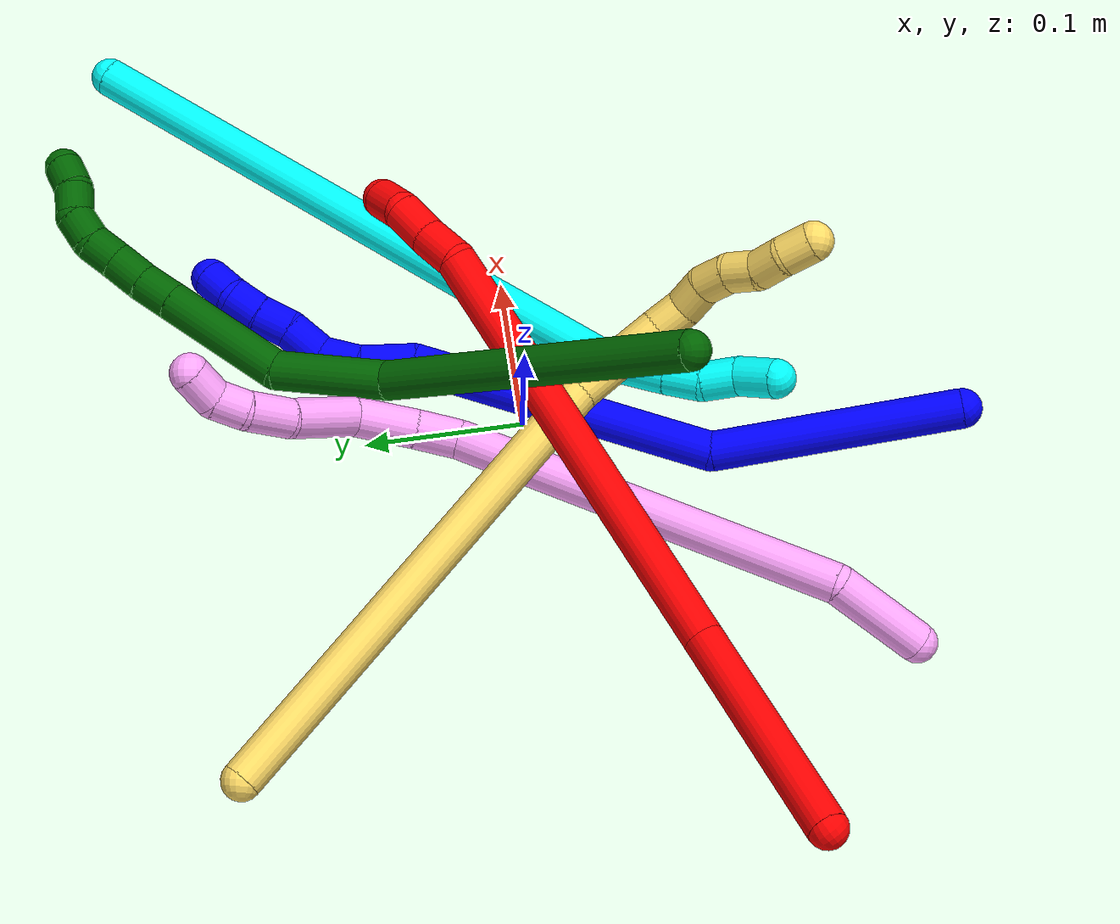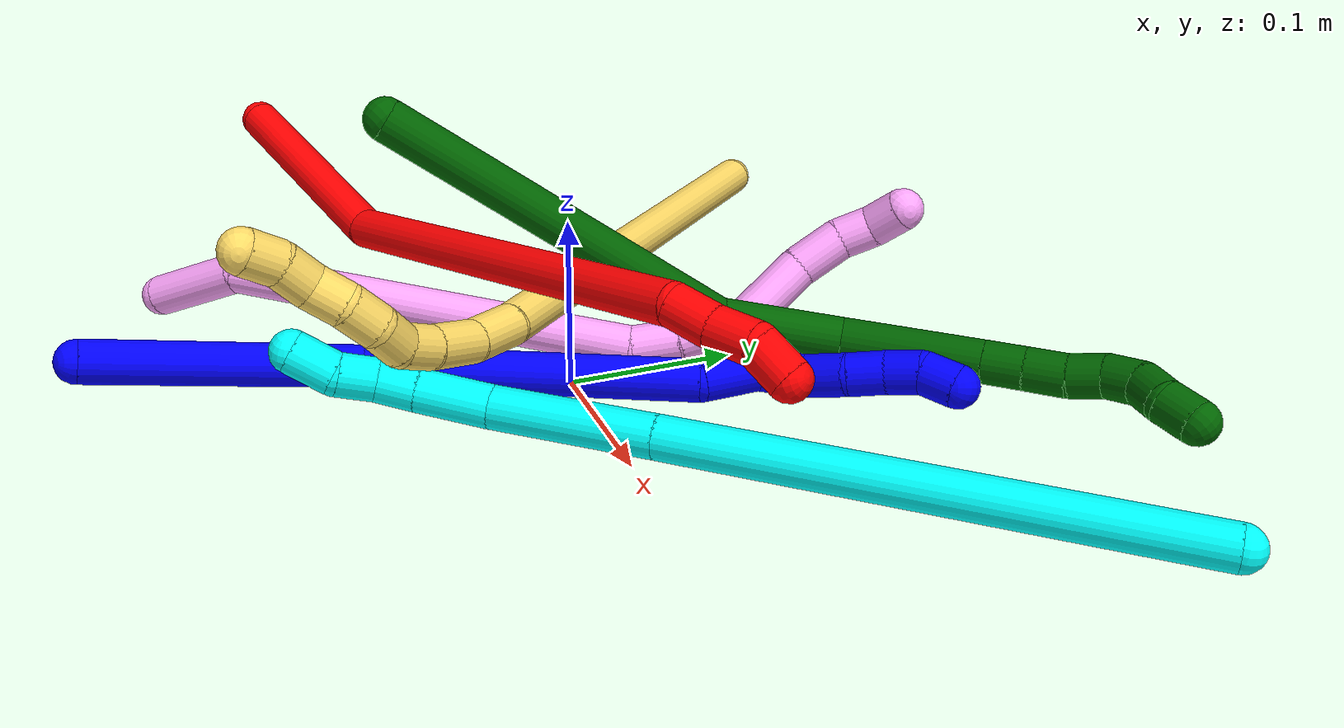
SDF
<sdf version="1.7">
 <world name="default">
  <plugin name="TubeGeneratorPlugin" filename="libtube_generator_plugin.so"/>
  <model name="photoneo_s_sensor">
   <static>1</static>
   <pose>0 0 2 1.57079 1.57079 3.14159</pose>
   <link name="link">
    <inertial><mass>0.1</mass></inertial>
    <sensor name="sensor" type="depth">
     <update_rate>30</update_rate>
     <camera>
      <horizontal_fov>1.22</horizontal_fov>
      <image><width>1920</width><height>1200</height><format>B8G8R8</format></image>
      <clip><near>0.1</near><far>4</far></clip>
      <depth_camera><output>points</output></depth_camera>
     </camera>
     <plugin name="camera_plugin" filename="libgazebo_ros_depth_camera.so">
      <baseline>0.2</baseline>
      <alwaysOn>1</alwaysOn>
      <updateRate>0.0</updateRate>
      <cameraName>camera_ir</cameraName>
      <imageTopicName>/camera/color/image_raw</imageTopicName>
      <cameraInfoTopicName>/camera/color/camera_info</cameraInfoTopicName>
      <depthImageTopicName>/camera/depth/image_raw</depthImageTopicName>
      <depthImageCameraInfoTopicName>/camera/depth/camera_info</depthImageCameraInfoTopicName>
      <pointCloudTopicName>/camera/depth/points</pointCloudTopicName>
      <frameName>fr_optical</frameName>
      <pointCloudCutoff>0.1</pointCloudCutoff>
      <pointCloudCutoffMax>2.0</pointCloudCutoffMax>
      <distortionK1>0</distortionK1>
      <distortionK2>0</distortionK2>
      <distortionK3>0</distortionK3>
      <distortionT1>0</distortionT1>
      <distortionT2>0</distortionT2>
      <CxPrime>0</CxPrime>
      <Cx>0</Cx>
      <Cy>0</Cy>
      <focalLength>0</focalLength>
      <hackBaseline>0</hackBaseline>
     </plugin>
    </sensor>
   </link>
  </model>
  <gravity>0 0 -9.8</gravity>
  <magnetic_field>6e-06 2.3e-05 -4.2e-05</magnetic_field>
  <atmosphere type="adiabatic"/>
  <physics name="default_physics" default="0" type="ode">
   <max_step_size>0.003</max_step_size>
   <real_time_factor>1</real_time_factor>
   <real_time_update_rate>1000</real_time_update_rate>
   <max_contacts>10000</max_contacts>
   <ode>
    <solver>
     <type>quick</type>
     <iters>100</iters>
     <sor>1.3</sor>
     <use_dynamic_moi_rescaling>0</use_dynamic_moi_rescaling>
    </solver>
    <constraints>
     <contact_max_correcting_vel>0</contact_max_correcting_vel>
     <contact_surface_layer>0.001</contact_surface_layer>
     <cfm>0</cfm>
     <erp>0.2</erp>
    </constraints>
   </ode>
  </physics>
  <scene><ambient>0.4 0.4 0.4 1</ambient><background>0.7 0.7 0.7 1</background><shadows>0</shadows></scene>
  <audio><device>default</device></audio>
  <spherical_coordinates>
   <surface_model>EARTH_WGS84</surface_model>
   <latitude_deg>0</latitude_deg>
   <longitude_deg>0</longitude_deg>
   <elevation>0</elevation>
   <heading_deg>0</heading_deg>
  </spherical_coordinates>
  <model name="bin">
   <static>1</static>
   <link name="bottom">
    <collision name="collision-bottom">
     <pose>0 0 -0.01 0 -0 0</pose>
     <geometry><box><size>0.8 0.6 0.02</size></box></geometry>
     <surface>
      <friction><ode><mu>100</mu><mu2>100</mu2></ode></friction>
      <contact><collide_bitmask>65535</collide_bitmask></contact>
     </surface>
    </collision>
   </link>
   <link name="west_wall">
    <collision name="collision-west_wall">
     <pose>-0.41 0 0.1 0 -0 0</pose>
     <geometry><box><size>0.02 0.6 0.2</size></box></geometry>
     <surface>
      <friction><ode><mu>100</mu><mu2>100</mu2></ode></friction>
      <contact><collide_bitmask>65535</collide_bitmask></contact>
     </surface>
    </collision>
   </link>
   <link name="east_wall">
    <collision name="collision-east_wall">
     <pose>0.41 0 0.1 0 -0 0</pose>
     <geometry><box><size>0.02 0.6 0.2</size></box></geometry>
     <surface>
      <friction><ode><mu>100</mu><mu2>100</mu2></ode></friction>
      <contact><collide_bitmask>65535</collide_bitmask></contact>
     </surface>
    </collision>
   </link>
   <link name="south_wall">
    <collision name="collision-south_wall">
     <pose>0 -0.31 0.1 0 -0 0</pose>
     <geometry><box><size>0.8 0.02 0.2</size></box></geometry>
     <surface>
      <friction><ode><mu>100</mu><mu2>100</mu2></ode></friction>
      <contact><collide_bitmask>65535</collide_bitmask></contact>
     </surface>
    </collision>
   </link>
   <link name="north_wall">
    <collision name="collision-north_wall">
     <pose>0 0.31 0.1 0 -0 0</pose>
     <geometry><box><size>0.8 0.02 0.2</size></box></geometry>
     <surface>
      <friction><ode><mu>100</mu><mu2>100</mu2></ode></friction>
      <contact><collide_bitmask>65535</collide_bitmask></contact>
     </surface>
    </collision>
   </link>
  </model>
  <model name="1">
   <static>0</static>
   <link name="1">
    <collision name="collision-cylinder-e_1_1_4">
     <pose>0.012643 0.027854 -0.071792 -2.77149 0.162729 -0.821664</pose>
     <geometry><cylinder><radius>0.0125</radius><length>0.156074</length></cylinder></geometry>
     <surface>
      <friction><ode><mu>1.16</mu><mu2>1.16</mu2><slip1>0</slip1><slip2>0</slip2></ode></friction>
      <contact><ode><kp>1e+06</kp><kd>1</kd><max_vel>0</max_vel><min_depth>0.001</min_depth></ode></contact>
     </surface>
    </collision>
    <visual name="visual-cylinder-e_1_1_4">
     <pose>0.012643 0.027854 -0.071792 -2.77149 0.162729 -0.821664</pose>
     <geometry><cylinder><radius>0.0125</radius><length>0.156074</length></cylinder></geometry>
     <material><ambient>0 0 1 1</ambient></material>
    </visual>
    <collision name="collision-cylinder-e_2_4_5">
     <pose>0.050913 0.124918 -0.206836 -2.31124 0.266813 -0.59108</pose>
     <geometry><cylinder><radius>0.0125</radius><length>0.194398</length></cylinder></geometry>
     <surface>
      <friction><ode><mu>1.16</mu><mu2>1.16</mu2><slip1>0</slip1><slip2>0</slip2></ode></friction>
      <contact><ode><kp>1e+06</kp><kd>1</kd><max_vel>0</max_vel><min_depth>0.001</min_depth></ode></contact>
     </surface>
    </collision>
    <visual name="visual-cylinder-e_2_4_5">
     <pose>0.050913 0.124918 -0.206836 -2.31124 0.266813 -0.59108</pose>
     <geometry><cylinder><radius>0.0125</radius><length>0.194398</length></cylinder></geometry>
     <material><ambient>0 0 1 1</ambient></material>
    </visual>
    <collision name="collision-cylinder-e_3_5_6">
     <pose>0.076388 0.203088 -0.284789 -2.59424 -0.008837 0.031478</pose>
     <geometry><cylinder><radius>0.0125</radius><length>0.034433</length></cylinder></geometry>
     <surface>
      <friction><ode><mu>1.16</mu><mu2>1.16</mu2><slip1>0</slip1><slip2>0</slip2></ode></friction>
      <contact><ode><kp>1e+06</kp><kd>1</kd><max_vel>0</max_vel><min_depth>0.001</min_depth></ode></contact>
     </surface>
    </collision>
    <visual name="visual-cylinder-e_3_5_6">
     <pose>0.076388 0.203088 -0.284789 -2.59424 -0.008837 0.031478</pose>
     <geometry><cylinder><radius>0.0125</radius><length>0.034433</length></cylinder></geometry>
     <material><ambient>0 0 1 1</ambient></material>
    </visual>
    <collision name="collision-cylinder-e_4_6_7">
     <pose>0.080929 0.220459 -0.308475 -2.38922 0.364242 -0.872541</pose>
     <geometry><cylinder><radius>0.0125</radius><length>0.026346</length></cylinder></geometry>
     <surface>
      <friction><ode><mu>1.16</mu><mu2>1.16</mu2><slip1>0</slip1><slip2>0</slip2></ode></friction>
      <contact><ode><kp>1e+06</kp><kd>1</kd><max_vel>0</max_vel><min_depth>0.001</min_depth></ode></contact>
     </surface>
    </collision>
    <visual name="visual-cylinder-e_4_6_7">
     <pose>0.080929 0.220459 -0.308475 -2.38922 0.364242 -0.872541</pose>
     <geometry><cylinder><radius>0.0125</radius><length>0.026346</length></cylinder></geometry>
     <material><ambient>0 0 1 1</ambient></material>
    </visual>
    <collision name="collision-cylinder-e_5_7_8">
     <pose>0.088546 0.24096 -0.321458 -1.89003 0.225786 -0.311229</pose>
     <geometry><cylinder><radius>0.0125</radius><length>0.026129</length></cylinder></geometry>
     <surface>
      <friction><ode><mu>1.16</mu><mu2>1.16</mu2><slip1>0</slip1><slip2>0</slip2></ode></friction>
      <contact><ode><kp>1e+06</kp><kd>1</kd><max_vel>0</max_vel><min_depth>0.001</min_depth></ode></contact>
     </surface>
    </collision>
    <visual name="visual-cylinder-e_5_7_8">
     <pose>0.088546 0.24096 -0.321458 -1.89003 0.225786 -0.311229</pose>
     <geometry><cylinder><radius>0.0125</radius><length>0.026129</length></cylinder></geometry>
     <material><ambient>0 0 1 1</ambient></material>
    </visual>
    <collision name="collision-cylinder-e_6_8_9">
     <pose>0.093443 0.262145 -0.331114 -2.12747 0.182011 -0.325648</pose>
     <geometry><cylinder><radius>0.0125</radius><length>0.021786</length></cylinder></geometry>
     <surface>
      <friction><ode><mu>1.16</mu><mu2>1.16</mu2><slip1>0</slip1><slip2>0</slip2></ode></friction>
      <contact><ode><kp>1e+06</kp><kd>1</kd><max_vel>0</max_vel><min_depth>0.001</min_depth></ode></contact>
     </surface>
    </collision>
    <visual name="visual-cylinder-e_6_8_9">
     <pose>0.093443 0.262145 -0.331114 -2.12747 0.182011 -0.325648</pose>
     <geometry><cylinder><radius>0.0125</radius><length>0.021786</length></cylinder></geometry>
     <material><ambient>0 0 1 1</ambient></material>
    </visual>
    <collision name="collision-cylinder-e_7_9_10">
     <pose>0.097977 0.280249 -0.340765 -1.98781 0.254426 -0.388155</pose>
     <geometry><cylinder><radius>0.0125</radius><length>0.020359</length></cylinder></geometry>
     <surface>
      <friction><ode><mu>1.16</mu><mu2>1.16</mu2><slip1>0</slip1><slip2>0</slip2></ode></friction>
      <contact><ode><kp>1e+06</kp><kd>1</kd><max_vel>0</max_vel><min_depth>0.001</min_depth></ode></contact>
     </surface>
    </collision>
    <visual name="visual-cylinder-e_7_9_10">
     <pose>0.097977 0.280249 -0.340765 -1.98781 0.254426 -0.388155</pose>
     <geometry><cylinder><radius>0.0125</radius><length>0.020359</length></cylinder></geometry>
     <material><ambient>0 0 1 1</ambient></material>
    </visual>
    <collision name="collision-cylinder-e_8_10_2">
     <pose>0.10663 0.296883 -0.347844 -1.95553 0.637193 -0.910263</pose>
     <geometry><cylinder><radius>0.0125</radius><length>0.020474</length></cylinder></geometry>
     <surface>
      <friction><ode><mu>1.16</mu><mu2>1.16</mu2><slip1>0</slip1><slip2>0</slip2></ode></friction>
      <contact><ode><kp>1e+06</kp><kd>1</kd><max_vel>0</max_vel><min_depth>0.001</min_depth></ode></contact>
     </surface>
    </collision>
    <visual name="visual-cylinder-e_8_10_2">
     <pose>0.10663 0.296883 -0.347844 -1.95553 0.637193 -0.910263</pose>
     <geometry><cylinder><radius>0.0125</radius><length>0.020474</length></cylinder></geometry>
     <material><ambient>0 0 1 1</ambient></material>
    </visual>
    <collision name="collision-sphere-2">
     <pose>0.11272 0.30451 -0.350932 0 -0 0</pose>
     <geometry><sphere><radius>0.0125</radius></sphere></geometry>
     <surface>
      <friction><ode><mu>1.16</mu><mu2>1.16</mu2><slip1>0</slip1><slip2>0</slip2></ode></friction>
      <contact><ode><kp>1e+06</kp><kd>1</kd><max_vel>0</max_vel><min_depth>0.001</min_depth></ode></contact>
     </surface>
    </collision>
    <visual name="visual-sphere-2">
     <pose>0.11272 0.30451 -0.350932 0 -0 0</pose>
     <geometry><sphere><radius>0.0125</radius></sphere></geometry>
     <material><ambient>0 0 1 1</ambient></material>
    </visual>
    <collision name="collision-sphere-10">
     <pose>0.100539 0.289257 -0.344756 0 -0 0</pose>
     <geometry><sphere><radius>0.0125</radius></sphere></geometry>
     <surface>
      <friction><ode><mu>1.16</mu><mu2>1.16</mu2><slip1>0</slip1><slip2>0</slip2></ode></friction>
      <contact><ode><kp>1e+06</kp><kd>1</kd><max_vel>0</max_vel><min_depth>0.001</min_depth></ode></contact>
     </surface>
    </collision>
    <visual name="visual-sphere-10">
     <pose>0.100539 0.289257 -0.344756 0 -0 0</pose>
     <geometry><sphere><radius>0.0125</radius></sphere></geometry>
     <material><ambient>0 0 1 1</ambient></material>
    </visual>
    <collision name="collision-sphere-9">
     <pose>0.095415 0.271241 -0.336775 0 -0 0</pose>
     <geometry><sphere><radius>0.0125</radius></sphere></geometry>
     <surface>
      <friction><ode><mu>1.16</mu><mu2>1.16</mu2><slip1>0</slip1><slip2>0</slip2></ode></friction>
      <contact><ode><kp>1e+06</kp><kd>1</kd><max_vel>0</max_vel><min_depth>0.001</min_depth></ode></contact>
     </surface>
    </collision>
    <visual name="visual-sphere-9">
     <pose>0.095415 0.271241 -0.336775 0 -0 0</pose>
     <geometry><sphere><radius>0.0125</radius></sphere></geometry>
     <material><ambient>0 0 1 1</ambient></material>
    </visual>
    <collision name="collision-sphere-4">
     <pose>0.025286 0.055708 -0.143584 0 -0 0</pose>
     <geometry><sphere><radius>0.0125</radius></sphere></geometry>
     <surface>
      <friction><ode><mu>1.16</mu><mu2>1.16</mu2><slip1>0</slip1><slip2>0</slip2></ode></friction>
      <contact><ode><kp>1e+06</kp><kd>1</kd><max_vel>0</max_vel><min_depth>0.001</min_depth></ode></contact>
     </surface>
    </collision>
    <visual name="visual-sphere-4">
     <pose>0.025286 0.055708 -0.143584 0 -0 0</pose>
     <geometry><sphere><radius>0.0125</radius></sphere></geometry>
     <material><ambient>0 0 1 1</ambient></material>
    </visual>
    <collision name="collision-sphere-1">
     <geometry><sphere><radius>0.0125</radius></sphere></geometry>
     <surface>
      <friction><ode><mu>1.16</mu><mu2>1.16</mu2><slip1>0</slip1><slip2>0</slip2></ode></friction>
      <contact><ode><kp>1e+06</kp><kd>1</kd><max_vel>0</max_vel><min_depth>0.001</min_depth></ode></contact>
     </surface>
    </collision>
    <visual name="visual-sphere-1">
     <geometry><sphere><radius>0.0125</radius></sphere></geometry>
     <material><ambient>0 0 1 1</ambient></material>
    </visual>
    <collision name="collision-sphere-8">
     <pose>0.091471 0.25305 -0.325454 0 -0 0</pose>
     <geometry><sphere><radius>0.0125</radius></sphere></geometry>
     <surface>
      <friction><ode><mu>1.16</mu><mu2>1.16</mu2><slip1>0</slip1><slip2>0</slip2></ode></friction>
      <contact><ode><kp>1e+06</kp><kd>1</kd><max_vel>0</max_vel><min_depth>0.001</min_depth></ode></contact>
     </surface>
    </collision>
    <visual name="visual-sphere-8">
     <pose>0.091471 0.25305 -0.325454 0 -0 0</pose>
     <geometry><sphere><radius>0.0125</radius></sphere></geometry>
     <material><ambient>0 0 1 1</ambient></material>
    </visual>
    <collision name="collision-sphere-5">
     <pose>0.076541 0.194128 -0.270088 0 -0 0</pose>
     <geometry><sphere><radius>0.0125</radius></sphere></geometry>
     <surface>
      <friction><ode><mu>1.16</mu><mu2>1.16</mu2><slip1>0</slip1><slip2>0</slip2></ode></friction>
      <contact><ode><kp>1e+06</kp><kd>1</kd><max_vel>0</max_vel><min_depth>0.001</min_depth></ode></contact>
     </surface>
    </collision>
    <visual name="visual-sphere-5">
     <pose>0.076541 0.194128 -0.270088 0 -0 0</pose>
     <geometry><sphere><radius>0.0125</radius></sphere></geometry>
     <material><ambient>0 0 1 1</ambient></material>
    </visual>
    <collision name="collision-sphere-6">
     <pose>0.076236 0.212047 -0.299489 0 -0 0</pose>
     <geometry><sphere><radius>0.0125</radius></sphere></geometry>
     <surface>
      <friction><ode><mu>1.16</mu><mu2>1.16</mu2><slip1>0</slip1><slip2>0</slip2></ode></friction>
      <contact><ode><kp>1e+06</kp><kd>1</kd><max_vel>0</max_vel><min_depth>0.001</min_depth></ode></contact>
     </surface>
    </collision>
    <visual name="visual-sphere-6">
     <pose>0.076236 0.212047 -0.299489 0 -0 0</pose>
     <geometry><sphere><radius>0.0125</radius></sphere></geometry>
     <material><ambient>0 0 1 1</ambient></material>
    </visual>
    <collision name="collision-sphere-7">
     <pose>0.085622 0.22887 -0.317462 0 -0 0</pose>
     <geometry><sphere><radius>0.0125</radius></sphere></geometry>
     <surface>
      <friction><ode><mu>1.16</mu><mu2>1.16</mu2><slip1>0</slip1><slip2>0</slip2></ode></friction>
      <contact><ode><kp>1e+06</kp><kd>1</kd><max_vel>0</max_vel><min_depth>0.001</min_depth></ode></contact>
     </surface>
    </collision>
    <visual name="visual-sphere-7">
     <pose>0.085622 0.22887 -0.317462 0 -0 0</pose>
     <geometry><sphere><radius>0.0125</radius></sphere></geometry>
     <material><ambient>0 0 1 1</ambient></material>
    </visual>
    <inertial>
     <pose>0.050321 0.130447 -0.198039 0 -0 0</pose>
     <mass>0.5</mass>
     <inertia>
      <ixx>0.000164</ixx>
      <ixy>0</ixy>
      <ixz>0</ixz>
      <iyy>-0.001025</iyy>
      <iyz>0</iyz>
      <izz>-0.000813</izz>
     </inertia>
    </inertial>
   </link>
   <pose>-0.045163 -0.265612 0.039503 1.11572 0.91354 -0.002705</pose>
  </model>
  <model name="2">
   <static>0</static>
   <link name="2">
    <collision name="collision-cylinder-e_1_1_4">
     <pose>0.026063 0.039855 -0.055391 -2.51788 0.364831 -1.03947</pose>
     <geometry><cylinder><radius>0.0125</radius><length>0.146095</length></cylinder></geometry>
     <surface>
      <friction><ode><mu>1.16</mu><mu2>1.16</mu2><slip1>0</slip1><slip2>0</slip2></ode></friction>
      <contact><ode><kp>1e+06</kp><kd>1</kd><max_vel>0</max_vel><min_depth>0.001</min_depth></ode></contact>
     </surface>
    </collision>
    <visual name="visual-cylinder-e_1_1_4">
     <pose>0.026063 0.039855 -0.055391 -2.51788 0.364831 -1.03947</pose>
     <geometry><cylinder><radius>0.0125</radius><length>0.146095</length></cylinder></geometry>
     <material><ambient>1 0 0 1</ambient></material>
    </visual>
    <collision name="collision-cylinder-e_2_4_5">
     <pose>0.070415 0.117326 -0.242901 -2.86422 0.132363 -0.886634</pose>
     <geometry><cylinder><radius>0.0125</radius><length>0.277162</length></cylinder></geometry>
     <surface>
      <friction><ode><mu>1.16</mu><mu2>1.16</mu2><slip1>0</slip1><slip2>0</slip2></ode></friction>
      <contact><ode><kp>1e+06</kp><kd>1</kd><max_vel>0</max_vel><min_depth>0.001</min_depth></ode></contact>
     </surface>
    </collision>
    <visual name="visual-cylinder-e_2_4_5">
     <pose>0.070415 0.117326 -0.242901 -2.86422 0.132363 -0.886634</pose>
     <geometry><cylinder><radius>0.0125</radius><length>0.277162</length></cylinder></geometry>
     <material><ambient>1 0 0 1</ambient></material>
    </visual>
    <collision name="collision-cylinder-e_3_5_6">
     <pose>0.095317 0.1593 -0.385757 -2.75605 0.518521 -1.87271</pose>
     <geometry><cylinder><radius>0.0125</radius><length>0.026686</length></cylinder></geometry>
     <surface>
      <friction><ode><mu>1.16</mu><mu2>1.16</mu2><slip1>0</slip1><slip2>0</slip2></ode></friction>
      <contact><ode><kp>1e+06</kp><kd>1</kd><max_vel>0</max_vel><min_depth>0.001</min_depth></ode></contact>
     </surface>
    </collision>
    <visual name="visual-cylinder-e_3_5_6">
     <pose>0.095317 0.1593 -0.385757 -2.75605 0.518521 -1.87271</pose>
     <geometry><cylinder><radius>0.0125</radius><length>0.026686</length></cylinder></geometry>
     <material><ambient>1 0 0 1</ambient></material>
    </visual>
    <collision name="collision-cylinder-e_4_6_7">
     <pose>0.106756 0.167134 -0.407972 -2.84749 0.382631 -1.83585</pose>
     <geometry><cylinder><radius>0.0125</radius><length>0.025853</length></cylinder></geometry>
     <surface>
      <friction><ode><mu>1.16</mu><mu2>1.16</mu2><slip1>0</slip1><slip2>0</slip2></ode></friction>
      <contact><ode><kp>1e+06</kp><kd>1</kd><max_vel>0</max_vel><min_depth>0.001</min_depth></ode></contact>
     </surface>
    </collision>
    <visual name="visual-cylinder-e_4_6_7">
     <pose>0.106756 0.167134 -0.407972 -2.84749 0.382631 -1.83585</pose>
     <geometry><cylinder><radius>0.0125</radius><length>0.025853</length></cylinder></geometry>
     <material><ambient>1 0 0 1</ambient></material>
    </visual>
    <collision name="collision-cylinder-e_5_7_2">
     <pose>0.119554 0.176723 -0.426199 -2.40568 0.719057 -1.54544</pose>
     <geometry><cylinder><radius>0.0125</radius><length>0.024205</length></cylinder></geometry>
     <surface>
      <friction><ode><mu>1.16</mu><mu2>1.16</mu2><slip1>0</slip1><slip2>0</slip2></ode></friction>
      <contact><ode><kp>1e+06</kp><kd>1</kd><max_vel>0</max_vel><min_depth>0.001</min_depth></ode></contact>
     </surface>
    </collision>
    <visual name="visual-cylinder-e_5_7_2">
     <pose>0.119554 0.176723 -0.426199 -2.40568 0.719057 -1.54544</pose>
     <geometry><cylinder><radius>0.0125</radius><length>0.024205</length></cylinder></geometry>
     <material><ambient>1 0 0 1</ambient></material>
    </visual>
    <collision name="collision-sphere-2">
     <pose>0.127525 0.182836 -0.432949 0 -0 0</pose>
     <geometry><sphere><radius>0.0125</radius></sphere></geometry>
     <surface>
      <friction><ode><mu>1.16</mu><mu2>1.16</mu2><slip1>0</slip1><slip2>0</slip2></ode></friction>
      <contact><ode><kp>1e+06</kp><kd>1</kd><max_vel>0</max_vel><min_depth>0.001</min_depth></ode></contact>
     </surface>
    </collision>
    <visual name="visual-sphere-2">
     <pose>0.127525 0.182836 -0.432949 0 -0 0</pose>
     <geometry><sphere><radius>0.0125</radius></sphere></geometry>
     <material><ambient>1 0 0 1</ambient></material>
    </visual>
    <collision name="collision-sphere-7">
     <pose>0.111582 0.17061 -0.419449 0 -0 0</pose>
     <geometry><sphere><radius>0.0125</radius></sphere></geometry>
     <surface>
      <friction><ode><mu>1.16</mu><mu2>1.16</mu2><slip1>0</slip1><slip2>0</slip2></ode></friction>
      <contact><ode><kp>1e+06</kp><kd>1</kd><max_vel>0</max_vel><min_depth>0.001</min_depth></ode></contact>
     </surface>
    </collision>
    <visual name="visual-sphere-7">
     <pose>0.111582 0.17061 -0.419449 0 -0 0</pose>
     <geometry><sphere><radius>0.0125</radius></sphere></geometry>
     <material><ambient>1 0 0 1</ambient></material>
    </visual>
    <collision name="collision-sphere-6">
     <pose>0.10193 0.163658 -0.396496 0 -0 0</pose>
     <geometry><sphere><radius>0.0125</radius></sphere></geometry>
     <surface>
      <friction><ode><mu>1.16</mu><mu2>1.16</mu2><slip1>0</slip1><slip2>0</slip2></ode></friction>
      <contact><ode><kp>1e+06</kp><kd>1</kd><max_vel>0</max_vel><min_depth>0.001</min_depth></ode></contact>
     </surface>
    </collision>
    <visual name="visual-sphere-6">
     <pose>0.10193 0.163658 -0.396496 0 -0 0</pose>
     <geometry><sphere><radius>0.0125</radius></sphere></geometry>
     <material><ambient>1 0 0 1</ambient></material>
    </visual>
    <collision name="collision-sphere-5">
     <pose>0.088704 0.154941 -0.375019 0 -0 0</pose>
     <geometry><sphere><radius>0.0125</radius></sphere></geometry>
     <surface>
      <friction><ode><mu>1.16</mu><mu2>1.16</mu2><slip1>0</slip1><slip2>0</slip2></ode></friction>
      <contact><ode><kp>1e+06</kp><kd>1</kd><max_vel>0</max_vel><min_depth>0.001</min_depth></ode></contact>
     </surface>
    </collision>
    <visual name="visual-sphere-5">
     <pose>0.088704 0.154941 -0.375019 0 -0 0</pose>
     <geometry><sphere><radius>0.0125</radius></sphere></geometry>
     <material><ambient>1 0 0 1</ambient></material>
    </visual>
    <collision name="collision-sphere-1">
     <geometry><sphere><radius>0.0125</radius></sphere></geometry>
     <surface>
      <friction><ode><mu>1.16</mu><mu2>1.16</mu2><slip1>0</slip1><slip2>0</slip2></ode></friction>
      <contact><ode><kp>1e+06</kp><kd>1</kd><max_vel>0</max_vel><min_depth>0.001</min_depth></ode></contact>
     </surface>
    </collision>
    <visual name="visual-sphere-1">
     <geometry><sphere><radius>0.0125</radius></sphere></geometry>
     <material><ambient>1 0 0 1</ambient></material>
    </visual>
    <collision name="collision-sphere-4">
     <pose>0.052125 0.079711 -0.110782 0 -0 0</pose>
     <geometry><sphere><radius>0.0125</radius></sphere></geometry>
     <surface>
      <friction><ode><mu>1.16</mu><mu2>1.16</mu2><slip1>0</slip1><slip2>0</slip2></ode></friction>
      <contact><ode><kp>1e+06</kp><kd>1</kd><max_vel>0</max_vel><min_depth>0.001</min_depth></ode></contact>
     </surface>
    </collision>
    <visual name="visual-sphere-4">
     <pose>0.052125 0.079711 -0.110782 0 -0 0</pose>
     <geometry><sphere><radius>0.0125</radius></sphere></geometry>
     <material><ambient>1 0 0 1</ambient></material>
    </visual>
    <inertial>
     <pose>0.063042 0.102381 -0.213146 0 -0 0</pose>
     <mass>0.5</mass>
     <inertia>
      <ixx>-0.000338</ixx>
      <ixy>0</ixy>
      <ixz>0</ixz>
      <iyy>-0.00267</iyy>
      <iyz>0</iyz>
      <izz>-0.001</izz>
     </inertia>
    </inertial>
   </link>
   <pose>-0.305227 -0.126104 0.079796 -2.21176 0.842094 1.62914</pose>
  </model>
  <model name="3">
   <static>0</static>
   <link name="3">
    <collision name="collision-cylinder-e_1_1_4">
     <pose>-0.105706 -0.096552 -0.022024 1.79507 -0.817981 -0.995577</pose>
     <geometry><cylinder><radius>0.0125</radius><length>0.289697</length></cylinder></geometry>
     <surface>
      <friction><ode><mu>1.16</mu><mu2>1.16</mu2><slip1>0</slip1><slip2>0</slip2></ode></friction>
      <contact><ode><kp>1e+06</kp><kd>1</kd><max_vel>0</max_vel><min_depth>0.001</min_depth></ode></contact>
     </surface>
    </collision>
    <visual name="visual-cylinder-e_1_1_4">
     <pose>-0.105706 -0.096552 -0.022024 1.79507 -0.817981 -0.995577</pose>
     <geometry><cylinder><radius>0.0125</radius><length>0.289697</length></cylinder></geometry>
     <material><ambient>0.003922 1 0.996078 1</ambient></material>
    </visual>
    <collision name="collision-cylinder-e_2_4_5">
     <pose>-0.245924 -0.225147 -0.051406 1.79648 -0.809675 -0.987226</pose>
     <geometry><cylinder><radius>0.0125</radius><length>0.09533</length></cylinder></geometry>
     <surface>
      <friction><ode><mu>1.16</mu><mu2>1.16</mu2><slip1>0</slip1><slip2>0</slip2></ode></friction>
      <contact><ode><kp>1e+06</kp><kd>1</kd><max_vel>0</max_vel><min_depth>0.001</min_depth></ode></contact>
     </surface>
    </collision>
    <visual name="visual-cylinder-e_2_4_5">
     <pose>-0.245924 -0.225147 -0.051406 1.79648 -0.809675 -0.987226</pose>
     <geometry><cylinder><radius>0.0125</radius><length>0.09533</length></cylinder></geometry>
     <material><ambient>0.003922 1 0.996078 1</ambient></material>
    </visual>
    <collision name="collision-cylinder-e_3_5_6">
     <pose>-0.292844 -0.274327 -0.057882 1.51945 -0.626024 -0.596548</pose>
     <geometry><cylinder><radius>0.0125</radius><length>0.042352</length></cylinder></geometry>
     <surface>
      <friction><ode><mu>1.16</mu><mu2>1.16</mu2><slip1>0</slip1><slip2>0</slip2></ode></friction>
      <contact><ode><kp>1e+06</kp><kd>1</kd><max_vel>0</max_vel><min_depth>0.001</min_depth></ode></contact>
     </surface>
    </collision>
    <visual name="visual-cylinder-e_3_5_6">
     <pose>-0.292844 -0.274327 -0.057882 1.51945 -0.626024 -0.596548</pose>
     <geometry><cylinder><radius>0.0125</radius><length>0.042352</length></cylinder></geometry>
     <material><ambient>0.003922 1 0.996078 1</ambient></material>
    </visual>
    <collision name="collision-cylinder-e_4_6_7">
     <pose>-0.311742 -0.301007 -0.05597 1.46318 -0.594607 -0.53686</pose>
     <geometry><cylinder><radius>0.0125</radius><length>0.023173</length></cylinder></geometry>
     <surface>
      <friction><ode><mu>1.16</mu><mu2>1.16</mu2><slip1>0</slip1><slip2>0</slip2></ode></friction>
      <contact><ode><kp>1e+06</kp><kd>1</kd><max_vel>0</max_vel><min_depth>0.001</min_depth></ode></contact>
     </surface>
    </collision>
    <visual name="visual-cylinder-e_4_6_7">
     <pose>-0.311742 -0.301007 -0.05597 1.46318 -0.594607 -0.53686</pose>
     <geometry><cylinder><radius>0.0125</radius><length>0.023173</length></cylinder></geometry>
     <material><ambient>0.003922 1 0.996078 1</ambient></material>
    </visual>
    <collision name="collision-cylinder-e_5_7_8">
     <pose>-0.321169 -0.321515 -0.052717 1.37085 -0.256661 -0.210247</pose>
     <geometry><cylinder><radius>0.0125</radius><length>0.023134</length></cylinder></geometry>
     <surface>
      <friction><ode><mu>1.16</mu><mu2>1.16</mu2><slip1>0</slip1><slip2>0</slip2></ode></friction>
      <contact><ode><kp>1e+06</kp><kd>1</kd><max_vel>0</max_vel><min_depth>0.001</min_depth></ode></contact>
     </surface>
    </collision>
    <visual name="visual-cylinder-e_5_7_8">
     <pose>-0.321169 -0.321515 -0.052717 1.37085 -0.256661 -0.210247</pose>
     <geometry><cylinder><radius>0.0125</radius><length>0.023134</length></cylinder></geometry>
     <material><ambient>0.003922 1 0.996078 1</ambient></material>
    </visual>
    <collision name="collision-cylinder-e_6_8_2">
     <pose>-0.331535 -0.342357 -0.045984 1.14243 -0.600028 -0.39251</pose>
     <geometry><cylinder><radius>0.0125</radius><length>0.026314</length></cylinder></geometry>
     <surface>
      <friction><ode><mu>1.16</mu><mu2>1.16</mu2><slip1>0</slip1><slip2>0</slip2></ode></friction>
      <contact><ode><kp>1e+06</kp><kd>1</kd><max_vel>0</max_vel><min_depth>0.001</min_depth></ode></contact>
     </surface>
    </collision>
    <visual name="visual-cylinder-e_6_8_2">
     <pose>-0.331535 -0.342357 -0.045984 1.14243 -0.600028 -0.39251</pose>
     <geometry><cylinder><radius>0.0125</radius><length>0.026314</length></cylinder></geometry>
     <material><ambient>0.003922 1 0.996078 1</ambient></material>
    </visual>
    <collision name="collision-sphere-2">
     <pose>-0.338964 -0.352235 -0.041474 0 -0 0</pose>
     <geometry><sphere><radius>0.0125</radius></sphere></geometry>
     <surface>
      <friction><ode><mu>1.16</mu><mu2>1.16</mu2><slip1>0</slip1><slip2>0</slip2></ode></friction>
      <contact><ode><kp>1e+06</kp><kd>1</kd><max_vel>0</max_vel><min_depth>0.001</min_depth></ode></contact>
     </surface>
    </collision>
    <visual name="visual-sphere-2">
     <pose>-0.338964 -0.352235 -0.041474 0 -0 0</pose>
     <geometry><sphere><radius>0.0125</radius></sphere></geometry>
     <material><ambient>0.003922 1 0.996078 1</ambient></material>
    </visual>
    <collision name="collision-sphere-4">
     <pose>-0.211411 -0.193105 -0.044049 0 -0 0</pose>
     <geometry><sphere><radius>0.0125</radius></sphere></geometry>
     <surface>
      <friction><ode><mu>1.16</mu><mu2>1.16</mu2><slip1>0</slip1><slip2>0</slip2></ode></friction>
      <contact><ode><kp>1e+06</kp><kd>1</kd><max_vel>0</max_vel><min_depth>0.001</min_depth></ode></contact>
     </surface>
    </collision>
    <visual name="visual-sphere-4">
     <pose>-0.211411 -0.193105 -0.044049 0 -0 0</pose>
     <geometry><sphere><radius>0.0125</radius></sphere></geometry>
     <material><ambient>0.003922 1 0.996078 1</ambient></material>
    </visual>
    <collision name="collision-sphere-1">
     <geometry><sphere><radius>0.0125</radius></sphere></geometry>
     <surface>
      <friction><ode><mu>1.16</mu><mu2>1.16</mu2><slip1>0</slip1><slip2>0</slip2></ode></friction>
      <contact><ode><kp>1e+06</kp><kd>1</kd><max_vel>0</max_vel><min_depth>0.001</min_depth></ode></contact>
     </surface>
    </collision>
    <visual name="visual-sphere-1">
     <geometry><sphere><radius>0.0125</radius></sphere></geometry>
     <material><ambient>0.003922 1 0.996078 1</ambient></material>
    </visual>
    <collision name="collision-sphere-8">
     <pose>-0.324105 -0.33248 -0.050495 0 -0 0</pose>
     <geometry><sphere><radius>0.0125</radius></sphere></geometry>
     <surface>
      <friction><ode><mu>1.16</mu><mu2>1.16</mu2><slip1>0</slip1><slip2>0</slip2></ode></friction>
      <contact><ode><kp>1e+06</kp><kd>1</kd><max_vel>0</max_vel><min_depth>0.001</min_depth></ode></contact>
     </surface>
    </collision>
    <visual name="visual-sphere-8">
     <pose>-0.324105 -0.33248 -0.050495 0 -0 0</pose>
     <geometry><sphere><radius>0.0125</radius></sphere></geometry>
     <material><ambient>0.003922 1 0.996078 1</ambient></material>
    </visual>
    <collision name="collision-sphere-5">
     <pose>-0.280437 -0.25719 -0.058762 0 -0 0</pose>
     <geometry><sphere><radius>0.0125</radius></sphere></geometry>
     <surface>
      <friction><ode><mu>1.16</mu><mu2>1.16</mu2><slip1>0</slip1><slip2>0</slip2></ode></friction>
      <contact><ode><kp>1e+06</kp><kd>1</kd><max_vel>0</max_vel><min_depth>0.001</min_depth></ode></contact>
     </surface>
    </collision>
    <visual name="visual-sphere-5">
     <pose>-0.280437 -0.25719 -0.058762 0 -0 0</pose>
     <geometry><sphere><radius>0.0125</radius></sphere></geometry>
     <material><ambient>0.003922 1 0.996078 1</ambient></material>
    </visual>
    <collision name="collision-sphere-6">
     <pose>-0.305252 -0.291465 -0.057001 0 -0 0</pose>
     <geometry><sphere><radius>0.0125</radius></sphere></geometry>
     <surface>
      <friction><ode><mu>1.16</mu><mu2>1.16</mu2><slip1>0</slip1><slip2>0</slip2></ode></friction>
      <contact><ode><kp>1e+06</kp><kd>1</kd><max_vel>0</max_vel><min_depth>0.001</min_depth></ode></contact>
     </surface>
    </collision>
    <visual name="visual-sphere-6">
     <pose>-0.305252 -0.291465 -0.057001 0 -0 0</pose>
     <geometry><sphere><radius>0.0125</radius></sphere></geometry>
     <material><ambient>0.003922 1 0.996078 1</ambient></material>
    </visual>
    <collision name="collision-sphere-7">
     <pose>-0.318233 -0.31055 -0.054939 0 -0 0</pose>
     <geometry><sphere><radius>0.0125</radius></sphere></geometry>
     <surface>
      <friction><ode><mu>1.16</mu><mu2>1.16</mu2><slip1>0</slip1><slip2>0</slip2></ode></friction>
      <contact><ode><kp>1e+06</kp><kd>1</kd><max_vel>0</max_vel><min_depth>0.001</min_depth></ode></contact>
     </surface>
    </collision>
    <visual name="visual-sphere-7">
     <pose>-0.318233 -0.31055 -0.054939 0 -0 0</pose>
     <geometry><sphere><radius>0.0125</radius></sphere></geometry>
     <material><ambient>0.003922 1 0.996078 1</ambient></material>
    </visual>
    <inertial>
     <pose>-0.179694 -0.168949 -0.034918 0 -0 0</pose>
     <mass>0.5</mass>
     <inertia>
      <ixx>-0.000447</ixx>
      <ixy>0</ixy>
      <ixz>0</ixz>
      <iyy>-0.000235</iyy>
      <iyz>0</iyz>
      <izz>0.002967</izz>
     </inertia>
    </inertial>
   </link>
   <pose>0.284922 0.234603 0.011499 -0.050605 0.161461 0.115366</pose>
  </model>
  <model name="4">
   <static>0</static>
   <link name="4">
    <collision name="collision-cylinder-e_1_1_4">
     <pose>0.00404 0.025318 0.016724 -0.987049 0.132352 -0.071269</pose>
     <geometry><cylinder><radius>0.0125</radius><length>0.061221</length></cylinder></geometry>
     <surface>
      <friction><ode><mu>1.16</mu><mu2>1.16</mu2><slip1>0</slip1><slip2>0</slip2></ode></friction>
      <contact><ode><kp>1e+06</kp><kd>1</kd><max_vel>0</max_vel><min_depth>0.001</min_depth></ode></contact>
     </surface>
    </collision>
    <visual name="visual-cylinder-e_1_1_4">
     <pose>0.00404 0.025318 0.016724 -0.987049 0.132352 -0.071269</pose>
     <geometry><cylinder><radius>0.0125</radius><length>0.061221</length></cylinder></geometry>
     <material><ambient>1 0.65098 0.996078 1</ambient></material>
    </visual>
    <collision name="collision-cylinder-e_2_4_5">
     <pose>0.08127 0.140519 0.082413 -1.07197 0.620769 -0.376531</pose>
     <geometry><cylinder><radius>0.0125</radius><length>0.251663</length></cylinder></geometry>
     <surface>
      <friction><ode><mu>1.16</mu><mu2>1.16</mu2><slip1>0</slip1><slip2>0</slip2></ode></friction>
      <contact><ode><kp>1e+06</kp><kd>1</kd><max_vel>0</max_vel><min_depth>0.001</min_depth></ode></contact>
     </surface>
    </collision>
    <visual name="visual-cylinder-e_2_4_5">
     <pose>0.08127 0.140519 0.082413 -1.07197 0.620769 -0.376531</pose>
     <geometry><cylinder><radius>0.0125</radius><length>0.251663</length></cylinder></geometry>
     <material><ambient>1 0.65098 0.996078 1</ambient></material>
    </visual>
    <collision name="collision-cylinder-e_3_5_6">
     <pose>0.159305 0.243271 0.134481 -1.33427 0.350711 -0.277296</pose>
     <geometry><cylinder><radius>0.0125</radius><length>0.028193</length></cylinder></geometry>
     <surface>
      <friction><ode><mu>1.16</mu><mu2>1.16</mu2><slip1>0</slip1><slip2>0</slip2></ode></friction>
      <contact><ode><kp>1e+06</kp><kd>1</kd><max_vel>0</max_vel><min_depth>0.001</min_depth></ode></contact>
     </surface>
    </collision>
    <visual name="visual-cylinder-e_3_5_6">
     <pose>0.159305 0.243271 0.134481 -1.33427 0.350711 -0.277296</pose>
     <geometry><cylinder><radius>0.0125</radius><length>0.028193</length></cylinder></geometry>
     <material><ambient>1 0.65098 0.996078 1</ambient></material>
    </visual>
    <collision name="collision-cylinder-e_4_6_7">
     <pose>0.168936 0.274979 0.140815 -1.40094 0.245459 -0.207245</pose>
     <geometry><cylinder><radius>0.0125</radius><length>0.039408</length></cylinder></geometry>
     <surface>
      <friction><ode><mu>1.16</mu><mu2>1.16</mu2><slip1>0</slip1><slip2>0</slip2></ode></friction>
      <contact><ode><kp>1e+06</kp><kd>1</kd><max_vel>0</max_vel><min_depth>0.001</min_depth></ode></contact>
     </surface>
    </collision>
    <visual name="visual-cylinder-e_4_6_7">
     <pose>0.168936 0.274979 0.140815 -1.40094 0.245459 -0.207245</pose>
     <geometry><cylinder><radius>0.0125</radius><length>0.039408</length></cylinder></geometry>
     <material><ambient>1 0.65098 0.996078 1</ambient></material>
    </visual>
    <collision name="collision-cylinder-e_5_7_8">
     <pose>0.169709 0.316738 0.140722 -1.7148 -0.171665 0.19819</pose>
     <geometry><cylinder><radius>0.0125</radius><length>0.047011</length></cylinder></geometry>
     <surface>
      <friction><ode><mu>1.16</mu><mu2>1.16</mu2><slip1>0</slip1><slip2>0</slip2></ode></friction>
      <contact><ode><kp>1e+06</kp><kd>1</kd><max_vel>0</max_vel><min_depth>0.001</min_depth></ode></contact>
     </surface>
    </collision>
    <visual name="visual-cylinder-e_5_7_8">
     <pose>0.169709 0.316738 0.140722 -1.7148 -0.171665 0.19819</pose>
     <geometry><cylinder><radius>0.0125</radius><length>0.047011</length></cylinder></geometry>
     <material><ambient>1 0.65098 0.996078 1</ambient></material>
    </visual>
    <collision name="collision-cylinder-e_6_8_9">
     <pose>0.164689 0.354538 0.138404 -1.50332 -0.067233 0.062846</pose>
     <geometry><cylinder><radius>0.0125</radius><length>0.029896</length></cylinder></geometry>
     <surface>
      <friction><ode><mu>1.16</mu><mu2>1.16</mu2><slip1>0</slip1><slip2>0</slip2></ode></friction>
      <contact><ode><kp>1e+06</kp><kd>1</kd><max_vel>0</max_vel><min_depth>0.001</min_depth></ode></contact>
     </surface>
    </collision>
    <visual name="visual-cylinder-e_6_8_9">
     <pose>0.164689 0.354538 0.138404 -1.50332 -0.067233 0.062846</pose>
     <geometry><cylinder><radius>0.0125</radius><length>0.029896</length></cylinder></geometry>
     <material><ambient>1 0.65098 0.996078 1</ambient></material>
    </visual>
    <collision name="collision-cylinder-e_7_9_10">
     <pose>0.164902 0.379395 0.142341 -1.28499 0.116488 -0.087227</pose>
     <geometry><cylinder><radius>0.0125</radius><length>0.020938</length></cylinder></geometry>
     <surface>
      <friction><ode><mu>1.16</mu><mu2>1.16</mu2><slip1>0</slip1><slip2>0</slip2></ode></friction>
      <contact><ode><kp>1e+06</kp><kd>1</kd><max_vel>0</max_vel><min_depth>0.001</min_depth></ode></contact>
     </surface>
    </collision>
    <visual name="visual-cylinder-e_7_9_10">
     <pose>0.164902 0.379395 0.142341 -1.28499 0.116488 -0.087227</pose>
     <geometry><cylinder><radius>0.0125</radius><length>0.020938</length></cylinder></geometry>
     <material><ambient>1 0.65098 0.996078 1</ambient></material>
    </visual>
    <collision name="collision-cylinder-e_8_10_2">
     <pose>0.164457 0.397715 0.151983 -0.893446 -0.153952 0.073858</pose>
     <geometry><cylinder><radius>0.0125</radius><length>0.021671</length></cylinder></geometry>
     <surface>
      <friction><ode><mu>1.16</mu><mu2>1.16</mu2><slip1>0</slip1><slip2>0</slip2></ode></friction>
      <contact><ode><kp>1e+06</kp><kd>1</kd><max_vel>0</max_vel><min_depth>0.001</min_depth></ode></contact>
     </surface>
    </collision>
    <visual name="visual-cylinder-e_8_10_2">
     <pose>0.164457 0.397715 0.151983 -0.893446 -0.153952 0.073858</pose>
     <geometry><cylinder><radius>0.0125</radius><length>0.021671</length></cylinder></geometry>
     <material><ambient>1 0.65098 0.996078 1</ambient></material>
    </visual>
    <collision name="collision-sphere-2">
     <pose>0.162795 0.406058 0.158694 0 -0 0</pose>
     <geometry><sphere><radius>0.0125</radius></sphere></geometry>
     <surface>
      <friction><ode><mu>1.16</mu><mu2>1.16</mu2><slip1>0</slip1><slip2>0</slip2></ode></friction>
      <contact><ode><kp>1e+06</kp><kd>1</kd><max_vel>0</max_vel><min_depth>0.001</min_depth></ode></contact>
     </surface>
    </collision>
    <visual name="visual-sphere-2">
     <pose>0.162795 0.406058 0.158694 0 -0 0</pose>
     <geometry><sphere><radius>0.0125</radius></sphere></geometry>
     <material><ambient>1 0.65098 0.996078 1</ambient></material>
    </visual>
    <collision name="collision-sphere-10">
     <pose>0.166118 0.389371 0.145273 0 -0 0</pose>
     <geometry><sphere><radius>0.0125</radius></sphere></geometry>
     <surface>
      <friction><ode><mu>1.16</mu><mu2>1.16</mu2><slip1>0</slip1><slip2>0</slip2></ode></friction>
      <contact><ode><kp>1e+06</kp><kd>1</kd><max_vel>0</max_vel><min_depth>0.001</min_depth></ode></contact>
     </surface>
    </collision>
    <visual name="visual-sphere-10">
     <pose>0.166118 0.389371 0.145273 0 -0 0</pose>
     <geometry><sphere><radius>0.0125</radius></sphere></geometry>
     <material><ambient>1 0.65098 0.996078 1</ambient></material>
    </visual>
    <collision name="collision-sphere-9">
     <pose>0.163685 0.369418 0.13941 0 -0 0</pose>
     <geometry><sphere><radius>0.0125</radius></sphere></geometry>
     <surface>
      <friction><ode><mu>1.16</mu><mu2>1.16</mu2><slip1>0</slip1><slip2>0</slip2></ode></friction>
      <contact><ode><kp>1e+06</kp><kd>1</kd><max_vel>0</max_vel><min_depth>0.001</min_depth></ode></contact>
     </surface>
    </collision>
    <visual name="visual-sphere-9">
     <pose>0.163685 0.369418 0.13941 0 -0 0</pose>
     <geometry><sphere><radius>0.0125</radius></sphere></geometry>
     <material><ambient>1 0.65098 0.996078 1</ambient></material>
    </visual>
    <collision name="collision-sphere-4">
     <pose>0.008079 0.050636 0.033447 0 -0 0</pose>
     <geometry><sphere><radius>0.0125</radius></sphere></geometry>
     <surface>
      <friction><ode><mu>1.16</mu><mu2>1.16</mu2><slip1>0</slip1><slip2>0</slip2></ode></friction>
      <contact><ode><kp>1e+06</kp><kd>1</kd><max_vel>0</max_vel><min_depth>0.001</min_depth></ode></contact>
     </surface>
    </collision>
    <visual name="visual-sphere-4">
     <pose>0.008079 0.050636 0.033447 0 -0 0</pose>
     <geometry><sphere><radius>0.0125</radius></sphere></geometry>
     <material><ambient>1 0.65098 0.996078 1</ambient></material>
    </visual>
    <collision name="collision-sphere-1">
     <geometry><sphere><radius>0.0125</radius></sphere></geometry>
     <surface>
      <friction><ode><mu>1.16</mu><mu2>1.16</mu2><slip1>0</slip1><slip2>0</slip2></ode></friction>
      <contact><ode><kp>1e+06</kp><kd>1</kd><max_vel>0</max_vel><min_depth>0.001</min_depth></ode></contact>
     </surface>
    </collision>
    <visual name="visual-sphere-1">
     <geometry><sphere><radius>0.0125</radius></sphere></geometry>
     <material><ambient>1 0.65098 0.996078 1</ambient></material>
    </visual>
    <collision name="collision-sphere-8">
     <pose>0.165693 0.339658 0.137398 0 -0 0</pose>
     <geometry><sphere><radius>0.0125</radius></sphere></geometry>
     <surface>
      <friction><ode><mu>1.16</mu><mu2>1.16</mu2><slip1>0</slip1><slip2>0</slip2></ode></friction>
      <contact><ode><kp>1e+06</kp><kd>1</kd><max_vel>0</max_vel><min_depth>0.001</min_depth></ode></contact>
     </surface>
    </collision>
    <visual name="visual-sphere-8">
     <pose>0.165693 0.339658 0.137398 0 -0 0</pose>
     <geometry><sphere><radius>0.0125</radius></sphere></geometry>
     <material><ambient>1 0.65098 0.996078 1</ambient></material>
    </visual>
    <collision name="collision-sphere-5">
     <pose>0.154461 0.230401 0.131379 0 -0 0</pose>
     <geometry><sphere><radius>0.0125</radius></sphere></geometry>
     <surface>
      <friction><ode><mu>1.16</mu><mu2>1.16</mu2><slip1>0</slip1><slip2>0</slip2></ode></friction>
      <contact><ode><kp>1e+06</kp><kd>1</kd><max_vel>0</max_vel><min_depth>0.001</min_depth></ode></contact>
     </surface>
    </collision>
    <visual name="visual-sphere-5">
     <pose>0.154461 0.230401 0.131379 0 -0 0</pose>
     <geometry><sphere><radius>0.0125</radius></sphere></geometry>
     <material><ambient>1 0.65098 0.996078 1</ambient></material>
    </visual>
    <collision name="collision-sphere-6">
     <pose>0.164148 0.256141 0.137584 0 -0 0</pose>
     <geometry><sphere><radius>0.0125</radius></sphere></geometry>
     <surface>
      <friction><ode><mu>1.16</mu><mu2>1.16</mu2><slip1>0</slip1><slip2>0</slip2></ode></friction>
      <contact><ode><kp>1e+06</kp><kd>1</kd><max_vel>0</max_vel><min_depth>0.001</min_depth></ode></contact>
     </surface>
    </collision>
    <visual name="visual-sphere-6">
     <pose>0.164148 0.256141 0.137584 0 -0 0</pose>
     <geometry><sphere><radius>0.0125</radius></sphere></geometry>
     <material><ambient>1 0.65098 0.996078 1</ambient></material>
    </visual>
    <collision name="collision-sphere-7">
     <pose>0.173724 0.293818 0.144045 0 -0 0</pose>
     <geometry><sphere><radius>0.0125</radius></sphere></geometry>
     <surface>
      <friction><ode><mu>1.16</mu><mu2>1.16</mu2><slip1>0</slip1><slip2>0</slip2></ode></friction>
      <contact><ode><kp>1e+06</kp><kd>1</kd><max_vel>0</max_vel><min_depth>0.001</min_depth></ode></contact>
     </surface>
    </collision>
    <visual name="visual-sphere-7">
     <pose>0.173724 0.293818 0.144045 0 -0 0</pose>
     <geometry><sphere><radius>0.0125</radius></sphere></geometry>
     <material><ambient>1 0.65098 0.996078 1</ambient></material>
    </visual>
    <inertial>
     <pose>0.103534 0.19332 0.096264 0 -0 0</pose>
     <mass>0.5</mass>
     <inertia>
      <ixx>0.00067</ixx>
      <ixy>0</ixy>
      <ixz>0</ixz>
      <iyy>0.000492</iyy>
      <iyz>0</iyz>
      <izz>-0.001768</izz>
     </inertia>
    </inertial>
   </link>
   <pose>-0.181196 -0.212747 0.011493 1.07322 1.04337 0.993827</pose>
  </model>
  <model name="5">
   <static>0</static>
   <link name="5">
    <collision name="collision-cylinder-e_1_1_4">
     <pose>-0.036419 -0.084703 -0.127364 2.55471 -0.233744 -0.741207</pose>
     <geometry><cylinder><radius>0.0125</radius><length>0.314468</length></cylinder></geometry>
     <surface>
      <friction><ode><mu>1.16</mu><mu2>1.16</mu2><slip1>0</slip1><slip2>0</slip2></ode></friction>
      <contact><ode><kp>1e+06</kp><kd>1</kd><max_vel>0</max_vel><min_depth>0.001</min_depth></ode></contact>
     </surface>
    </collision>
    <visual name="visual-cylinder-e_1_1_4">
     <pose>-0.036419 -0.084703 -0.127364 2.55471 -0.233744 -0.741207</pose>
     <geometry><cylinder><radius>0.0125</radius><length>0.314468</length></cylinder></geometry>
     <material><ambient>1 0.858824 0.4 1</ambient></material>
    </visual>
    <collision name="collision-cylinder-e_2_4_5">
     <pose>-0.076104 -0.180134 -0.266061 2.38353 -0.206324 -0.508615</pose>
     <geometry><cylinder><radius>0.0125</radius><length>0.031887</length></cylinder></geometry>
     <surface>
      <friction><ode><mu>1.16</mu><mu2>1.16</mu2><slip1>0</slip1><slip2>0</slip2></ode></friction>
      <contact><ode><kp>1e+06</kp><kd>1</kd><max_vel>0</max_vel><min_depth>0.001</min_depth></ode></contact>
     </surface>
    </collision>
    <visual name="visual-cylinder-e_2_4_5">
     <pose>-0.076104 -0.180134 -0.266061 2.38353 -0.206324 -0.508615</pose>
     <geometry><cylinder><radius>0.0125</radius><length>0.031887</length></cylinder></geometry>
     <material><ambient>1 0.858824 0.4 1</ambient></material>
    </visual>
    <collision name="collision-cylinder-e_3_5_6">
     <pose>-0.079613 -0.202221 -0.28805 2.32439 -0.015626 -0.036087</pose>
     <geometry><cylinder><radius>0.0125</radius><length>0.031154</length></cylinder></geometry>
     <surface>
      <friction><ode><mu>1.16</mu><mu2>1.16</mu2><slip1>0</slip1><slip2>0</slip2></ode></friction>
      <contact><ode><kp>1e+06</kp><kd>1</kd><max_vel>0</max_vel><min_depth>0.001</min_depth></ode></contact>
     </surface>
    </collision>
    <visual name="visual-cylinder-e_3_5_6">
     <pose>-0.079613 -0.202221 -0.28805 2.32439 -0.015626 -0.036087</pose>
     <geometry><cylinder><radius>0.0125</radius><length>0.031154</length></cylinder></geometry>
     <material><ambient>1 0.858824 0.4 1</ambient></material>
    </visual>
    <collision name="collision-cylinder-e_4_6_7">
     <pose>-0.078469 -0.221603 -0.305314 2.25954 0.132722 0.279745</pose>
     <geometry><cylinder><radius>0.0125</radius><length>0.020971</length></cylinder></geometry>
     <surface>
      <friction><ode><mu>1.16</mu><mu2>1.16</mu2><slip1>0</slip1><slip2>0</slip2></ode></friction>
      <contact><ode><kp>1e+06</kp><kd>1</kd><max_vel>0</max_vel><min_depth>0.001</min_depth></ode></contact>
     </surface>
    </collision>
    <visual name="visual-cylinder-e_4_6_7">
     <pose>-0.078469 -0.221603 -0.305314 2.25954 0.132722 0.279745</pose>
     <geometry><cylinder><radius>0.0125</radius><length>0.020971</length></cylinder></geometry>
     <material><ambient>1 0.858824 0.4 1</ambient></material>
    </visual>
    <collision name="collision-cylinder-e_5_7_8">
     <pose>-0.071265 -0.235855 -0.317957 2.34068 0.590746 1.24642</pose>
     <geometry><cylinder><radius>0.0125</radius><length>0.020888</length></cylinder></geometry>
     <surface>
      <friction><ode><mu>1.16</mu><mu2>1.16</mu2><slip1>0</slip1><slip2>0</slip2></ode></friction>
      <contact><ode><kp>1e+06</kp><kd>1</kd><max_vel>0</max_vel><min_depth>0.001</min_depth></ode></contact>
     </surface>
    </collision>
    <visual name="visual-cylinder-e_5_7_8">
     <pose>-0.071265 -0.235855 -0.317957 2.34068 0.590746 1.24642</pose>
     <geometry><cylinder><radius>0.0125</radius><length>0.020888</length></cylinder></geometry>
     <material><ambient>1 0.858824 0.4 1</ambient></material>
    </visual>
    <collision name="collision-cylinder-e_6_8_9">
     <pose>-0.059944 -0.250202 -0.326874 1.91159 0.568495 0.784342</pose>
     <geometry><cylinder><radius>0.0125</radius><length>0.020443</length></cylinder></geometry>
     <surface>
      <friction><ode><mu>1.16</mu><mu2>1.16</mu2><slip1>0</slip1><slip2>0</slip2></ode></friction>
      <contact><ode><kp>1e+06</kp><kd>1</kd><max_vel>0</max_vel><min_depth>0.001</min_depth></ode></contact>
     </surface>
    </collision>
    <visual name="visual-cylinder-e_6_8_9">
     <pose>-0.059944 -0.250202 -0.326874 1.91159 0.568495 0.784342</pose>
     <geometry><cylinder><radius>0.0125</radius><length>0.020443</length></cylinder></geometry>
     <material><ambient>1 0.858824 0.4 1</ambient></material>
    </visual>
    <collision name="collision-cylinder-e_7_9_10">
     <pose>-0.050197 -0.267397 -0.329881 1.58493 0.437386 0.443411</pose>
     <geometry><cylinder><radius>0.0125</radius><length>0.020043</length></cylinder></geometry>
     <surface>
      <friction><ode><mu>1.16</mu><mu2>1.16</mu2><slip1>0</slip1><slip2>0</slip2></ode></friction>
      <contact><ode><kp>1e+06</kp><kd>1</kd><max_vel>0</max_vel><min_depth>0.001</min_depth></ode></contact>
     </surface>
    </collision>
    <visual name="visual-cylinder-e_7_9_10">
     <pose>-0.050197 -0.267397 -0.329881 1.58493 0.437386 0.443411</pose>
     <geometry><cylinder><radius>0.0125</radius><length>0.020043</length></cylinder></geometry>
     <material><ambient>1 0.858824 0.4 1</ambient></material>
    </visual>
    <collision name="collision-cylinder-e_8_10_11">
     <pose>-0.040366 -0.284104 -0.333335 1.98181 0.59109 0.870215</pose>
     <geometry><cylinder><radius>0.0125</radius><length>0.020047</length></cylinder></geometry>
     <surface>
      <friction><ode><mu>1.16</mu><mu2>1.16</mu2><slip1>0</slip1><slip2>0</slip2></ode></friction>
      <contact><ode><kp>1e+06</kp><kd>1</kd><max_vel>0</max_vel><min_depth>0.001</min_depth></ode></contact>
     </surface>
    </collision>
    <visual name="visual-cylinder-e_8_10_11">
     <pose>-0.040366 -0.284104 -0.333335 1.98181 0.59109 0.870215</pose>
     <geometry><cylinder><radius>0.0125</radius><length>0.020047</length></cylinder></geometry>
     <material><ambient>1 0.858824 0.4 1</ambient></material>
    </visual>
    <collision name="collision-cylinder-e_9_11_2">
     <pose>-0.031776 -0.300396 -0.340776 2.01441 0.303549 0.474918</pose>
     <geometry><cylinder><radius>0.0125</radius><length>0.020098</length></cylinder></geometry>
     <surface>
      <friction><ode><mu>1.16</mu><mu2>1.16</mu2><slip1>0</slip1><slip2>0</slip2></ode></friction>
      <contact><ode><kp>1e+06</kp><kd>1</kd><max_vel>0</max_vel><min_depth>0.001</min_depth></ode></contact>
     </surface>
    </collision>
    <visual name="visual-cylinder-e_9_11_2">
     <pose>-0.031776 -0.300396 -0.340776 2.01441 0.303549 0.474918</pose>
     <geometry><cylinder><radius>0.0125</radius><length>0.020098</length></cylinder></geometry>
     <material><ambient>1 0.858824 0.4 1</ambient></material>
    </visual>
    <collision name="collision-sphere-2">
     <pose>-0.028773 -0.309057 -0.344892 0 -0 0</pose>
     <geometry><sphere><radius>0.0125</radius></sphere></geometry>
     <surface>
      <friction><ode><mu>1.16</mu><mu2>1.16</mu2><slip1>0</slip1><slip2>0</slip2></ode></friction>
      <contact><ode><kp>1e+06</kp><kd>1</kd><max_vel>0</max_vel><min_depth>0.001</min_depth></ode></contact>
     </surface>
    </collision>
    <visual name="visual-sphere-2">
     <pose>-0.028773 -0.309057 -0.344892 0 -0 0</pose>
     <geometry><sphere><radius>0.0125</radius></sphere></geometry>
     <material><ambient>1 0.858824 0.4 1</ambient></material>
    </visual>
    <collision name="collision-sphere-11">
     <pose>-0.03478 -0.291734 -0.33666 0 -0 0</pose>
     <geometry><sphere><radius>0.0125</radius></sphere></geometry>
     <surface>
      <friction><ode><mu>1.16</mu><mu2>1.16</mu2><slip1>0</slip1><slip2>0</slip2></ode></friction>
      <contact><ode><kp>1e+06</kp><kd>1</kd><max_vel>0</max_vel><min_depth>0.001</min_depth></ode></contact>
     </surface>
    </collision>
    <visual name="visual-sphere-11">
     <pose>-0.03478 -0.291734 -0.33666 0 -0 0</pose>
     <geometry><sphere><radius>0.0125</radius></sphere></geometry>
     <material><ambient>1 0.858824 0.4 1</ambient></material>
    </visual>
    <collision name="collision-sphere-10">
     <pose>-0.045952 -0.276475 -0.330009 0 -0 0</pose>
     <geometry><sphere><radius>0.0125</radius></sphere></geometry>
     <surface>
      <friction><ode><mu>1.16</mu><mu2>1.16</mu2><slip1>0</slip1><slip2>0</slip2></ode></friction>
      <contact><ode><kp>1e+06</kp><kd>1</kd><max_vel>0</max_vel><min_depth>0.001</min_depth></ode></contact>
     </surface>
    </collision>
    <visual name="visual-sphere-10">
     <pose>-0.045952 -0.276475 -0.330009 0 -0 0</pose>
     <geometry><sphere><radius>0.0125</radius></sphere></geometry>
     <material><ambient>1 0.858824 0.4 1</ambient></material>
    </visual>
    <collision name="collision-sphere-9">
     <pose>-0.054442 -0.25832 -0.329753 0 -0 0</pose>
     <geometry><sphere><radius>0.0125</radius></sphere></geometry>
     <surface>
      <friction><ode><mu>1.16</mu><mu2>1.16</mu2><slip1>0</slip1><slip2>0</slip2></ode></friction>
      <contact><ode><kp>1e+06</kp><kd>1</kd><max_vel>0</max_vel><min_depth>0.001</min_depth></ode></contact>
     </surface>
    </collision>
    <visual name="visual-sphere-9">
     <pose>-0.054442 -0.25832 -0.329753 0 -0 0</pose>
     <geometry><sphere><radius>0.0125</radius></sphere></geometry>
     <material><ambient>1 0.858824 0.4 1</ambient></material>
    </visual>
    <collision name="collision-sphere-4">
     <pose>-0.072838 -0.169405 -0.254729 0 -0 0</pose>
     <geometry><sphere><radius>0.0125</radius></sphere></geometry>
     <surface>
      <friction><ode><mu>1.16</mu><mu2>1.16</mu2><slip1>0</slip1><slip2>0</slip2></ode></friction>
      <contact><ode><kp>1e+06</kp><kd>1</kd><max_vel>0</max_vel><min_depth>0.001</min_depth></ode></contact>
     </surface>
    </collision>
    <visual name="visual-sphere-4">
     <pose>-0.072838 -0.169405 -0.254729 0 -0 0</pose>
     <geometry><sphere><radius>0.0125</radius></sphere></geometry>
     <material><ambient>1 0.858824 0.4 1</ambient></material>
    </visual>
    <collision name="collision-sphere-1">
     <geometry><sphere><radius>0.0125</radius></sphere></geometry>
     <surface>
      <friction><ode><mu>1.16</mu><mu2>1.16</mu2><slip1>0</slip1><slip2>0</slip2></ode></friction>
      <contact><ode><kp>1e+06</kp><kd>1</kd><max_vel>0</max_vel><min_depth>0.001</min_depth></ode></contact>
     </surface>
    </collision>
    <visual name="visual-sphere-1">
     <geometry><sphere><radius>0.0125</radius></sphere></geometry>
     <material><ambient>1 0.858824 0.4 1</ambient></material>
    </visual>
    <collision name="collision-sphere-8">
     <pose>-0.065447 -0.242083 -0.323995 0 -0 0</pose>
     <geometry><sphere><radius>0.0125</radius></sphere></geometry>
     <surface>
      <friction><ode><mu>1.16</mu><mu2>1.16</mu2><slip1>0</slip1><slip2>0</slip2></ode></friction>
      <contact><ode><kp>1e+06</kp><kd>1</kd><max_vel>0</max_vel><min_depth>0.001</min_depth></ode></contact>
     </surface>
    </collision>
    <visual name="visual-sphere-8">
     <pose>-0.065447 -0.242083 -0.323995 0 -0 0</pose>
     <geometry><sphere><radius>0.0125</radius></sphere></geometry>
     <material><ambient>1 0.858824 0.4 1</ambient></material>
    </visual>
    <collision name="collision-sphere-5">
     <pose>-0.07937 -0.190863 -0.277393 0 -0 0</pose>
     <geometry><sphere><radius>0.0125</radius></sphere></geometry>
     <surface>
      <friction><ode><mu>1.16</mu><mu2>1.16</mu2><slip1>0</slip1><slip2>0</slip2></ode></friction>
      <contact><ode><kp>1e+06</kp><kd>1</kd><max_vel>0</max_vel><min_depth>0.001</min_depth></ode></contact>
     </surface>
    </collision>
    <visual name="visual-sphere-5">
     <pose>-0.07937 -0.190863 -0.277393 0 -0 0</pose>
     <geometry><sphere><radius>0.0125</radius></sphere></geometry>
     <material><ambient>1 0.858824 0.4 1</ambient></material>
    </visual>
    <collision name="collision-sphere-6">
     <pose>-0.079857 -0.213579 -0.298708 0 -0 0</pose>
     <geometry><sphere><radius>0.0125</radius></sphere></geometry>
     <surface>
      <friction><ode><mu>1.16</mu><mu2>1.16</mu2><slip1>0</slip1><slip2>0</slip2></ode></friction>
      <contact><ode><kp>1e+06</kp><kd>1</kd><max_vel>0</max_vel><min_depth>0.001</min_depth></ode></contact>
     </surface>
    </collision>
    <visual name="visual-sphere-6">
     <pose>-0.079857 -0.213579 -0.298708 0 -0 0</pose>
     <geometry><sphere><radius>0.0125</radius></sphere></geometry>
     <material><ambient>1 0.858824 0.4 1</ambient></material>
    </visual>
    <collision name="collision-sphere-7">
     <pose>-0.077082 -0.229627 -0.311919 0 -0 0</pose>
     <geometry><sphere><radius>0.0125</radius></sphere></geometry>
     <surface>
      <friction><ode><mu>1.16</mu><mu2>1.16</mu2><slip1>0</slip1><slip2>0</slip2></ode></friction>
      <contact><ode><kp>1e+06</kp><kd>1</kd><max_vel>0</max_vel><min_depth>0.001</min_depth></ode></contact>
     </surface>
    </collision>
    <visual name="visual-sphere-7">
     <pose>-0.077082 -0.229627 -0.311919 0 -0 0</pose>
     <geometry><sphere><radius>0.0125</radius></sphere></geometry>
     <material><ambient>1 0.858824 0.4 1</ambient></material>
    </visual>
    <inertial>
     <pose>-0.046346 -0.140923 -0.194759 0 -0 0</pose>
     <mass>0.5</mass>
     <inertia>
      <ixx>0.000172</ixx>
      <ixy>0</ixy>
      <ixz>0</ixz>
      <iyy>-0.003111</iyy>
      <iyz>0</iyz>
      <izz>0.001988</izz>
     </inertia>
    </inertial>
   </link>
   <pose>-0.214115 0.197414 0.027196 -2.6708 -1.28709 2.42502</pose>
  </model>
  <model name="6">
   <static>0</static>
   <link name="6">
    <collision name="collision-cylinder-e_1_1_4">
     <pose>0.094953 0.039711 0.036211 -0.831467 1.05577 -0.503879</pose>
     <geometry><cylinder><radius>0.0125</radius><length>0.218213</length></cylinder></geometry>
     <surface>
      <friction><ode><mu>1.16</mu><mu2>1.16</mu2><slip1>0</slip1><slip2>0</slip2></ode></friction>
      <contact><ode><kp>1e+06</kp><kd>1</kd><max_vel>0</max_vel><min_depth>0.001</min_depth></ode></contact>
     </surface>
    </collision>
    <visual name="visual-cylinder-e_1_1_4">
     <pose>0.094953 0.039711 0.036211 -0.831467 1.05577 -0.503879</pose>
     <geometry><cylinder><radius>0.0125</radius><length>0.218213</length></cylinder></geometry>
     <material><ambient>0 0.392157 0.003922 1</ambient></material>
    </visual>
    <collision name="collision-cylinder-e_2_4_5">
     <pose>0.217746 0.084334 0.095409 -0.210547 0.869579 -0.098069</pose>
     <geometry><cylinder><radius>0.0125</radius><length>0.072874</length></cylinder></geometry>
     <surface>
      <friction><ode><mu>1.16</mu><mu2>1.16</mu2><slip1>0</slip1><slip2>0</slip2></ode></friction>
      <contact><ode><kp>1e+06</kp><kd>1</kd><max_vel>0</max_vel><min_depth>0.001</min_depth></ode></contact>
     </surface>
    </collision>
    <visual name="visual-cylinder-e_2_4_5">
     <pose>0.217746 0.084334 0.095409 -0.210547 0.869579 -0.098069</pose>
     <geometry><cylinder><radius>0.0125</radius><length>0.072874</length></cylinder></geometry>
     <material><ambient>0 0.392157 0.003922 1</ambient></material>
    </visual>
    <collision name="collision-cylinder-e_3_5_6">
     <pose>0.278876 0.076571 0.138669 0.558841 0.947962 0.292279</pose>
     <geometry><cylinder><radius>0.0125</radius><length>0.081972</length></cylinder></geometry>
     <surface>
      <friction><ode><mu>1.16</mu><mu2>1.16</mu2><slip1>0</slip1><slip2>0</slip2></ode></friction>
      <contact><ode><kp>1e+06</kp><kd>1</kd><max_vel>0</max_vel><min_depth>0.001</min_depth></ode></contact>
     </surface>
    </collision>
    <visual name="visual-cylinder-e_3_5_6">
     <pose>0.278876 0.076571 0.138669 0.558841 0.947962 0.292279</pose>
     <geometry><cylinder><radius>0.0125</radius><length>0.081972</length></cylinder></geometry>
     <material><ambient>0 0.392157 0.003922 1</ambient></material>
    </visual>
    <collision name="collision-cylinder-e_4_6_7">
     <pose>0.321568 0.06037 0.164636 0.55407 0.951763 0.291026</pose>
     <geometry><cylinder><radius>0.0125</radius><length>0.023088</length></cylinder></geometry>
     <surface>
      <friction><ode><mu>1.16</mu><mu2>1.16</mu2><slip1>0</slip1><slip2>0</slip2></ode></friction>
      <contact><ode><kp>1e+06</kp><kd>1</kd><max_vel>0</max_vel><min_depth>0.001</min_depth></ode></contact>
     </surface>
    </collision>
    <visual name="visual-cylinder-e_4_6_7">
     <pose>0.321568 0.06037 0.164636 0.55407 0.951763 0.291026</pose>
     <geometry><cylinder><radius>0.0125</radius><length>0.023088</length></cylinder></geometry>
     <material><ambient>0 0.392157 0.003922 1</ambient></material>
    </visual>
    <collision name="collision-cylinder-e_5_7_8">
     <pose>0.340426 0.052452 0.175674 0.688369 0.93932 0.35992</pose>
     <geometry><cylinder><radius>0.0125</radius><length>0.023431</length></cylinder></geometry>
     <surface>
      <friction><ode><mu>1.16</mu><mu2>1.16</mu2><slip1>0</slip1><slip2>0</slip2></ode></friction>
      <contact><ode><kp>1e+06</kp><kd>1</kd><max_vel>0</max_vel><min_depth>0.001</min_depth></ode></contact>
     </surface>
    </collision>
    <visual name="visual-cylinder-e_5_7_8">
     <pose>0.340426 0.052452 0.175674 0.688369 0.93932 0.35992</pose>
     <geometry><cylinder><radius>0.0125</radius><length>0.023431</length></cylinder></geometry>
     <material><ambient>0 0.392157 0.003922 1</ambient></material>
    </visual>
    <collision name="collision-cylinder-e_6_8_9">
     <pose>0.356879 0.043696 0.186888 0.638822 0.763137 0.263862</pose>
     <geometry><cylinder><radius>0.0125</radius><length>0.020247</length></cylinder></geometry>
     <surface>
      <friction><ode><mu>1.16</mu><mu2>1.16</mu2><slip1>0</slip1><slip2>0</slip2></ode></friction>
      <contact><ode><kp>1e+06</kp><kd>1</kd><max_vel>0</max_vel><min_depth>0.001</min_depth></ode></contact>
     </surface>
    </collision>
    <visual name="visual-cylinder-e_6_8_9">
     <pose>0.356879 0.043696 0.186888 0.638822 0.763137 0.263862</pose>
     <geometry><cylinder><radius>0.0125</radius><length>0.020247</length></cylinder></geometry>
     <material><ambient>0 0.392157 0.003922 1</ambient></material>
    </visual>
    <collision name="collision-cylinder-e_7_9_10">
     <pose>0.371476 0.033271 0.195422 1.15726 0.854048 0.577822</pose>
     <geometry><cylinder><radius>0.0125</radius><length>0.020158</length></cylinder></geometry>
     <surface>
      <friction><ode><mu>1.16</mu><mu2>1.16</mu2><slip1>0</slip1><slip2>0</slip2></ode></friction>
      <contact><ode><kp>1e+06</kp><kd>1</kd><max_vel>0</max_vel><min_depth>0.001</min_depth></ode></contact>
     </surface>
    </collision>
    <visual name="visual-cylinder-e_7_9_10">
     <pose>0.371476 0.033271 0.195422 1.15726 0.854048 0.577822</pose>
     <geometry><cylinder><radius>0.0125</radius><length>0.020158</length></cylinder></geometry>
     <material><ambient>0 0.392157 0.003922 1</ambient></material>
    </visual>
    <collision name="collision-cylinder-e_8_10_11">
     <pose>0.385824 0.020211 0.195731 1.89506 0.740718 0.990478</pose>
     <geometry><cylinder><radius>0.0125</radius><length>0.020004</length></cylinder></geometry>
     <surface>
      <friction><ode><mu>1.16</mu><mu2>1.16</mu2><slip1>0</slip1><slip2>0</slip2></ode></friction>
      <contact><ode><kp>1e+06</kp><kd>1</kd><max_vel>0</max_vel><min_depth>0.001</min_depth></ode></contact>
     </surface>
    </collision>
    <visual name="visual-cylinder-e_8_10_11">
     <pose>0.385824 0.020211 0.195731 1.89506 0.740718 0.990478</pose>
     <geometry><cylinder><radius>0.0125</radius><length>0.020004</length></cylinder></geometry>
     <material><ambient>0 0.392157 0.003922 1</ambient></material>
    </visual>
    <collision name="collision-cylinder-e_9_11_2">
     <pose>0.401351 0.008412 0.193182 1.61192 1.0698 1.10623</pose>
     <geometry><cylinder><radius>0.0125</radius><length>0.020013</length></cylinder></geometry>
     <surface>
      <friction><ode><mu>1.16</mu><mu2>1.16</mu2><slip1>0</slip1><slip2>0</slip2></ode></friction>
      <contact><ode><kp>1e+06</kp><kd>1</kd><max_vel>0</max_vel><min_depth>0.001</min_depth></ode></contact>
     </surface>
    </collision>
    <visual name="visual-cylinder-e_9_11_2">
     <pose>0.401351 0.008412 0.193182 1.61192 1.0698 1.10623</pose>
     <geometry><cylinder><radius>0.0125</radius><length>0.020013</length></cylinder></geometry>
     <material><ambient>0 0.392157 0.003922 1</ambient></material>
    </visual>
    <collision name="collision-sphere-2">
     <pose>0.410128 0.00361 0.192984 0 -0 0</pose>
     <geometry><sphere><radius>0.0125</radius></sphere></geometry>
     <surface>
      <friction><ode><mu>1.16</mu><mu2>1.16</mu2><slip1>0</slip1><slip2>0</slip2></ode></friction>
      <contact><ode><kp>1e+06</kp><kd>1</kd><max_vel>0</max_vel><min_depth>0.001</min_depth></ode></contact>
     </surface>
    </collision>
    <visual name="visual-sphere-2">
     <pose>0.410128 0.00361 0.192984 0 -0 0</pose>
     <geometry><sphere><radius>0.0125</radius></sphere></geometry>
     <material><ambient>0 0.392157 0.003922 1</ambient></material>
    </visual>
    <collision name="collision-sphere-11">
     <pose>0.392574 0.013214 0.193379 0 -0 0</pose>
     <geometry><sphere><radius>0.0125</radius></sphere></geometry>
     <surface>
      <friction><ode><mu>1.16</mu><mu2>1.16</mu2><slip1>0</slip1><slip2>0</slip2></ode></friction>
      <contact><ode><kp>1e+06</kp><kd>1</kd><max_vel>0</max_vel><min_depth>0.001</min_depth></ode></contact>
     </surface>
    </collision>
    <visual name="visual-sphere-11">
     <pose>0.392574 0.013214 0.193379 0 -0 0</pose>
     <geometry><sphere><radius>0.0125</radius></sphere></geometry>
     <material><ambient>0 0.392157 0.003922 1</ambient></material>
    </visual>
    <collision name="collision-sphere-10">
     <pose>0.379075 0.027208 0.198083 0 -0 0</pose>
     <geometry><sphere><radius>0.0125</radius></sphere></geometry>
     <surface>
      <friction><ode><mu>1.16</mu><mu2>1.16</mu2><slip1>0</slip1><slip2>0</slip2></ode></friction>
      <contact><ode><kp>1e+06</kp><kd>1</kd><max_vel>0</max_vel><min_depth>0.001</min_depth></ode></contact>
     </surface>
    </collision>
    <visual name="visual-sphere-10">
     <pose>0.379075 0.027208 0.198083 0 -0 0</pose>
     <geometry><sphere><radius>0.0125</radius></sphere></geometry>
     <material><ambient>0 0.392157 0.003922 1</ambient></material>
    </visual>
    <collision name="collision-sphere-9">
     <pose>0.363877 0.039334 0.192761 0 -0 0</pose>
     <geometry><sphere><radius>0.0125</radius></sphere></geometry>
     <surface>
      <friction><ode><mu>1.16</mu><mu2>1.16</mu2><slip1>0</slip1><slip2>0</slip2></ode></friction>
      <contact><ode><kp>1e+06</kp><kd>1</kd><max_vel>0</max_vel><min_depth>0.001</min_depth></ode></contact>
     </surface>
    </collision>
    <visual name="visual-sphere-9">
     <pose>0.363877 0.039334 0.192761 0 -0 0</pose>
     <geometry><sphere><radius>0.0125</radius></sphere></geometry>
     <material><ambient>0 0.392157 0.003922 1</ambient></material>
    </visual>
    <collision name="collision-sphere-4">
     <pose>0.189907 0.079421 0.072421 0 -0 0</pose>
     <geometry><sphere><radius>0.0125</radius></sphere></geometry>
     <surface>
      <friction><ode><mu>1.16</mu><mu2>1.16</mu2><slip1>0</slip1><slip2>0</slip2></ode></friction>
      <contact><ode><kp>1e+06</kp><kd>1</kd><max_vel>0</max_vel><min_depth>0.001</min_depth></ode></contact>
     </surface>
    </collision>
    <visual name="visual-sphere-4">
     <pose>0.189907 0.079421 0.072421 0 -0 0</pose>
     <geometry><sphere><radius>0.0125</radius></sphere></geometry>
     <material><ambient>0 0.392157 0.003922 1</ambient></material>
    </visual>
    <collision name="collision-sphere-1">
     <geometry><sphere><radius>0.0125</radius></sphere></geometry>
     <surface>
      <friction><ode><mu>1.16</mu><mu2>1.16</mu2><slip1>0</slip1><slip2>0</slip2></ode></friction>
      <contact><ode><kp>1e+06</kp><kd>1</kd><max_vel>0</max_vel><min_depth>0.001</min_depth></ode></contact>
     </surface>
    </collision>
    <visual name="visual-sphere-1">
     <geometry><sphere><radius>0.0125</radius></sphere></geometry>
     <material><ambient>0 0.392157 0.003922 1</ambient></material>
    </visual>
    <collision name="collision-sphere-8">
     <pose>0.349882 0.048058 0.181015 0 -0 0</pose>
     <geometry><sphere><radius>0.0125</radius></sphere></geometry>
     <surface>
      <friction><ode><mu>1.16</mu><mu2>1.16</mu2><slip1>0</slip1><slip2>0</slip2></ode></friction>
      <contact><ode><kp>1e+06</kp><kd>1</kd><max_vel>0</max_vel><min_depth>0.001</min_depth></ode></contact>
     </surface>
    </collision>
    <visual name="visual-sphere-8">
     <pose>0.349882 0.048058 0.181015 0 -0 0</pose>
     <geometry><sphere><radius>0.0125</radius></sphere></geometry>
     <material><ambient>0 0.392157 0.003922 1</ambient></material>
    </visual>
    <collision name="collision-sphere-5">
     <pose>0.245586 0.089247 0.118397 0 -0 0</pose>
     <geometry><sphere><radius>0.0125</radius></sphere></geometry>
     <surface>
      <friction><ode><mu>1.16</mu><mu2>1.16</mu2><slip1>0</slip1><slip2>0</slip2></ode></friction>
      <contact><ode><kp>1e+06</kp><kd>1</kd><max_vel>0</max_vel><min_depth>0.001</min_depth></ode></contact>
     </surface>
    </collision>
    <visual name="visual-sphere-5">
     <pose>0.245586 0.089247 0.118397 0 -0 0</pose>
     <geometry><sphere><radius>0.0125</radius></sphere></geometry>
     <material><ambient>0 0.392157 0.003922 1</ambient></material>
    </visual>
    <collision name="collision-sphere-6">
     <pose>0.312166 0.063894 0.15894 0 -0 0</pose>
     <geometry><sphere><radius>0.0125</radius></sphere></geometry>
     <surface>
      <friction><ode><mu>1.16</mu><mu2>1.16</mu2><slip1>0</slip1><slip2>0</slip2></ode></friction>
      <contact><ode><kp>1e+06</kp><kd>1</kd><max_vel>0</max_vel><min_depth>0.001</min_depth></ode></contact>
     </surface>
    </collision>
    <visual name="visual-sphere-6">
     <pose>0.312166 0.063894 0.15894 0 -0 0</pose>
     <geometry><sphere><radius>0.0125</radius></sphere></geometry>
     <material><ambient>0 0.392157 0.003922 1</ambient></material>
    </visual>
    <collision name="collision-sphere-7">
     <pose>0.33097 0.056846 0.170332 0 -0 0</pose>
     <geometry><sphere><radius>0.0125</radius></sphere></geometry>
     <surface>
      <friction><ode><mu>1.16</mu><mu2>1.16</mu2><slip1>0</slip1><slip2>0</slip2></ode></friction>
      <contact><ode><kp>1e+06</kp><kd>1</kd><max_vel>0</max_vel><min_depth>0.001</min_depth></ode></contact>
     </surface>
    </collision>
    <visual name="visual-sphere-7">
     <pose>0.33097 0.056846 0.170332 0 -0 0</pose>
     <geometry><sphere><radius>0.0125</radius></sphere></geometry>
     <material><ambient>0 0.392157 0.003922 1</ambient></material>
    </visual>
    <inertial>
     <pose>0.210626 0.051677 0.099287 0 -0 0</pose>
     <mass>0.5</mass>
     <inertia>
      <ixx>0.000265</ixx>
      <ixy>0</ixy>
      <ixz>0</ixz>
      <iyy>0.000677</iyy>
      <iyz>0</iyz>
      <izz>-0.001123</izz>
     </inertia>
    </inertial>
   </link>
   <pose>-0.038975 -0.089882 0.157938 -0.924986 0.571442 0.599249</pose>
  </model>
 </world>
</sdf>
